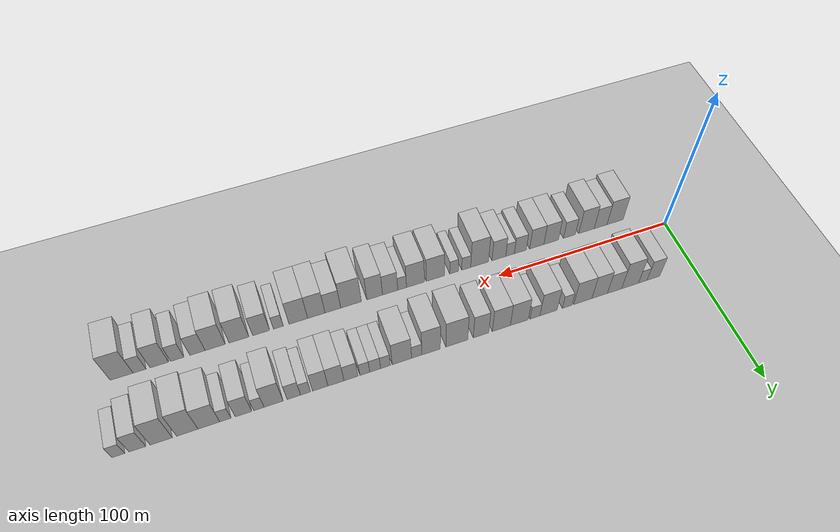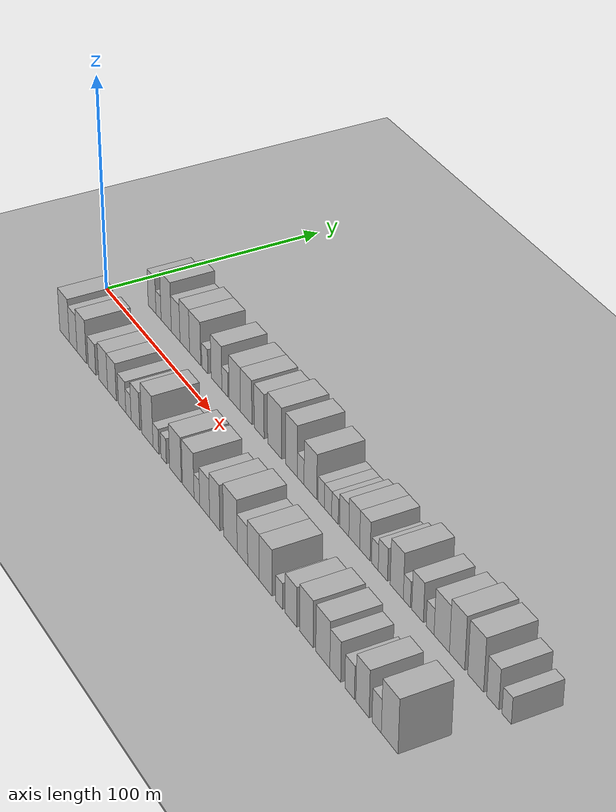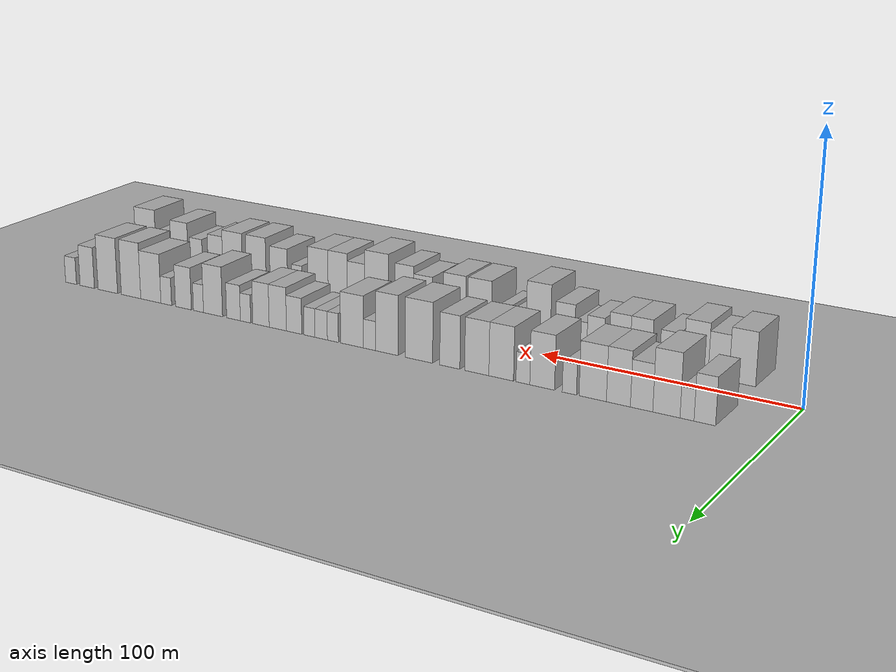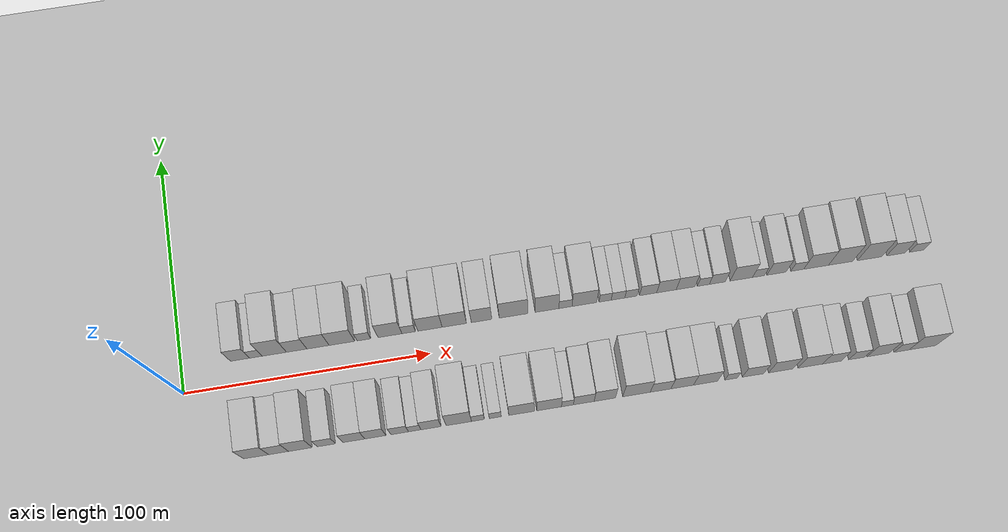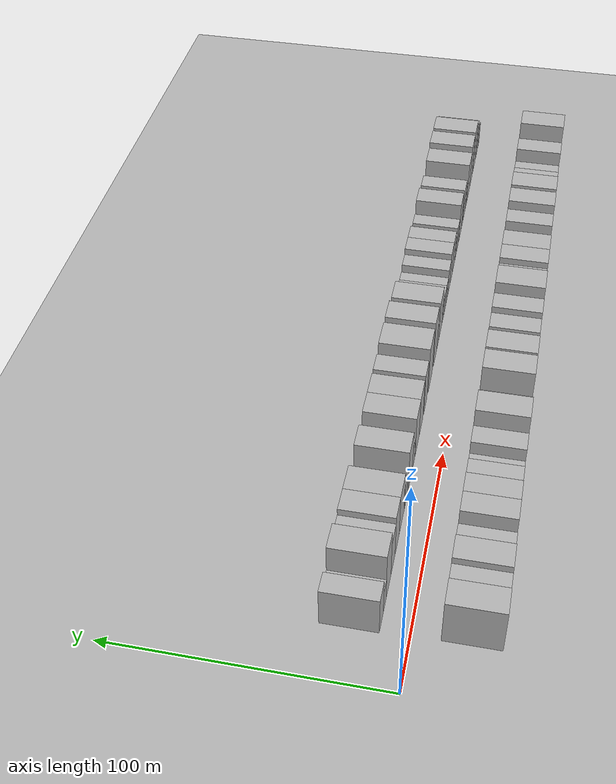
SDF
<?xml version="1.0" encoding="utf-8"?>

<sdf version="1.6">

   <world name="default">

      <gui fullscreen="0">

         <camera name="user_camera">

            <pose>-15 0 4.57585 0 0 0</pose>

            <view_controller>orbit</view_controller>

         </camera>

      </gui>

      <scene>

         <sky>

           <clouds>

             <speed>12</speed>

           </clouds>

         </sky>

         <ambient>0.4 0.4 0.4 1</ambient>

         <background>0.7 0.7 0.7 1</background>

         <shadows>1</shadows>

      </scene>

      <gravity>0 0 -9.8066</gravity>

      <magnetic_field>6e-06 2.3e-05 -4.2e-05</magnetic_field>

      <physics default="0" name="default_physics" type="ode">

         <ode>

            <solver>

               <type>quick</type>

               <iters>10</iters>

               <sor>1.0</sor>

               <use_dynamic_moi_rescaling>0</use_dynamic_moi_rescaling>

            </solver>

            <constraints>

               <cfm>0</cfm>

               <erp>0.2</erp>

               <contact_max_correcting_vel>100</contact_max_correcting_vel>

               <contact_surface_layer>0.001</contact_surface_layer>

            </constraints>

         </ode>

         <max_step_size>0.004</max_step_size>

         <real_time_factor>1</real_time_factor>

         <real_time_update_rate>250</real_time_update_rate>

      </physics>

      <light name="sun" type="directional">

         <cast_shadows>1</cast_shadows>

         <pose>0 0 10 0 0 0</pose>

         <diffuse>0.8 0.8 0.8 1</diffuse>

         <specular>0.2 0.2 0.2 1</specular>

         <attenuation>

            <range>1000</range>

            <constant>0.9</constant>

            <linear>0.01</linear>

            <quadratic>0.001</quadratic>

         </attenuation>

         <direction>-0.5 0.1 -0.9</direction>

      </light>

      <include>

         <name>ground_plane_1</name>

         <uri>model://HANNAS_ground_plane</uri>

         <pose>0 0 0  0 0 0</pose>

      </include>

      <include>

         <name>ground_plane_2</name>

         <uri>model://HANNAS_ground_plane</uri>

         <pose>100 0 0  0 0 0</pose>

      </include>

      <model name="building_1">

         <static>1</static>

         <pose frame="">23.8435 20.0000 0 0.000000 0.000000 1.570796</pose>

         <link name="link">

            <pose frame="">0 0 9.00 0 0 0</pose>

            <collision name="collision">

               <geometry>

                  <box>

                     <size>20.0000 7.6871 18.0000</size>

                  </box>

               </geometry>

               <max_contacts>10</max_contacts>

               <surface>

                  <contact>

                     <ode/>

                  </contact>

                  <bounce/>

                  <friction>

                     <torsional>

                        <ode/>

                     </torsional>

                     <ode/>

                  </friction>

               </surface>

            </collision>

            <visual name="visual">

               <cast_shadows>0</cast_shadows>

               <geometry>

                  <box>

                     <size>20.0000 7.6871 18.0000</size>

                  </box>

               </geometry>

               <material>

                  <script>

                     <uri>model://HANNAS_wall/materials/scripts</uri>

                     <uri>model://HANNAS_wall/materials/textures</uri>

                     <name>vrc/HANNAS_wall</name>

                  </script>

               </material>

            </visual>

            <self_collide>0</self_collide>

            <enable_wind>0</enable_wind>

            <kinematic>0</kinematic>

         </link>

      </model>

      <model name="building_2">

         <static>1</static>

         <pose frame="">30.2150 20.0000 0 0.000000 0.000000 1.570796</pose>

         <link name="link">

            <pose frame="">0 0 6.00 0 0 0</pose>

            <collision name="collision">

               <geometry>

                  <box>

                     <size>20.0000 5.0559 12.0000</size>

                  </box>

               </geometry>

               <max_contacts>10</max_contacts>

               <surface>

                  <contact>

                     <ode/>

                  </contact>

                  <bounce/>

                  <friction>

                     <torsional>

                        <ode/>

                     </torsional>

                     <ode/>

                  </friction>

               </surface>

            </collision>

            <visual name="visual">

               <cast_shadows>0</cast_shadows>

               <geometry>

                  <box>

                     <size>20.0000 5.0559 12.0000</size>

                  </box>

               </geometry>

               <material>

                  <script>

                     <uri>model://HANNAS_wall/materials/scripts</uri>

                     <uri>model://HANNAS_wall/materials/textures</uri>

                     <name>vrc/HANNAS_wall</name>

                  </script>

               </material>

            </visual>

            <self_collide>0</self_collide>

            <enable_wind>0</enable_wind>

            <kinematic>0</kinematic>

         </link>

      </model>

      <model name="building_3">

         <static>1</static>

         <pose frame="">37.7222 20.0000 0 0.000000 0.000000 1.570796</pose>

         <link name="link">

            <pose frame="">0 0 12.00 0 0 0</pose>

            <collision name="collision">

               <geometry>

                  <box>

                     <size>20.0000 9.9584 24.0000</size>

                  </box>

               </geometry>

               <max_contacts>10</max_contacts>

               <surface>

                  <contact>

                     <ode/>

                  </contact>

                  <bounce/>

                  <friction>

                     <torsional>

                        <ode/>

                     </torsional>

                     <ode/>

                  </friction>

               </surface>

            </collision>

            <visual name="visual">

               <cast_shadows>0</cast_shadows>

               <geometry>

                  <box>

                     <size>20.0000 9.9584 24.0000</size>

                  </box>

               </geometry>

               <material>

                  <script>

                     <uri>model://HANNAS_wall/materials/scripts</uri>

                     <uri>model://HANNAS_wall/materials/textures</uri>

                     <name>vrc/HANNAS_wall</name>

                  </script>

               </material>

            </visual>

            <self_collide>0</self_collide>

            <enable_wind>0</enable_wind>

            <kinematic>0</kinematic>

         </link>

      </model>

      <model name="building_4">

         <static>1</static>

         <pose frame="">46.8498 20.0000 0 0.000000 0.000000 1.570796</pose>

         <link name="link">

            <pose frame="">0 0 9.00 0 0 0</pose>

            <collision name="collision">

               <geometry>

                  <box>

                     <size>20.0000 8.2967 18.0000</size>

                  </box>

               </geometry>

               <max_contacts>10</max_contacts>

               <surface>

                  <contact>

                     <ode/>

                  </contact>

                  <bounce/>

                  <friction>

                     <torsional>

                        <ode/>

                     </torsional>

                     <ode/>

                  </friction>

               </surface>

            </collision>

            <visual name="visual">

               <cast_shadows>0</cast_shadows>

               <geometry>

                  <box>

                     <size>20.0000 8.2967 18.0000</size>

                  </box>

               </geometry>

               <material>

                  <script>

                     <uri>model://HANNAS_wall/materials/scripts</uri>

                     <uri>model://HANNAS_wall/materials/textures</uri>

                     <name>vrc/HANNAS_wall</name>

                  </script>

               </material>

            </visual>

            <self_collide>0</self_collide>

            <enable_wind>0</enable_wind>

            <kinematic>0</kinematic>

         </link>

      </model>

      <model name="building_5">

         <static>1</static>

         <pose frame="">55.5143 20.0000 0 0.000000 0.000000 1.570796</pose>

         <link name="link">

            <pose frame="">0 0 10.50 0 0 0</pose>

            <collision name="collision">

               <geometry>

                  <box>

                     <size>20.0000 9.0323 21.0000</size>

                  </box>

               </geometry>

               <max_contacts>10</max_contacts>

               <surface>

                  <contact>

                     <ode/>

                  </contact>

                  <bounce/>

                  <friction>

                     <torsional>

                        <ode/>

                     </torsional>

                     <ode/>

                  </friction>

               </surface>

            </collision>

            <visual name="visual">

               <cast_shadows>0</cast_shadows>

               <geometry>

                  <box>

                     <size>20.0000 9.0323 21.0000</size>

                  </box>

               </geometry>

               <material>

                  <script>

                     <uri>model://HANNAS_wall/materials/scripts</uri>

                     <uri>model://HANNAS_wall/materials/textures</uri>

                     <name>vrc/HANNAS_wall</name>

                  </script>

               </material>

            </visual>

            <self_collide>0</self_collide>

            <enable_wind>0</enable_wind>

            <kinematic>0</kinematic>

         </link>

      </model>

      <model name="building_6">

         <static>1</static>

         <pose frame="">65.2510 20.0000 0 0.000000 0.000000 1.570796</pose>

         <link name="link">

            <pose frame="">0 0 10.50 0 0 0</pose>

            <collision name="collision">

               <geometry>

                  <box>

                     <size>20.0000 10.4411 21.0000</size>

                  </box>

               </geometry>

               <max_contacts>10</max_contacts>

               <surface>

                  <contact>

                     <ode/>

                  </contact>

                  <bounce/>

                  <friction>

                     <torsional>

                        <ode/>

                     </torsional>

                     <ode/>

                  </friction>

               </surface>

            </collision>

            <visual name="visual">

               <cast_shadows>0</cast_shadows>

               <geometry>

                  <box>

                     <size>20.0000 10.4411 21.0000</size>

                  </box>

               </geometry>

               <material>

                  <script>

                     <uri>model://HANNAS_wall/materials/scripts</uri>

                     <uri>model://HANNAS_wall/materials/textures</uri>

                     <name>vrc/HANNAS_wall</name>

                  </script>

               </material>

            </visual>

            <self_collide>0</self_collide>

            <enable_wind>0</enable_wind>

            <kinematic>0</kinematic>

         </link>

      </model>

      <model name="building_7">

         <static>1</static>

         <pose frame="">74.2370 20.0000 0 0.000000 0.000000 1.570796</pose>

         <link name="link">

            <pose frame="">0 0 6.00 0 0 0</pose>

            <collision name="collision">

               <geometry>

                  <box>

                     <size>20.0000 5.5309 12.0000</size>

                  </box>

               </geometry>

               <max_contacts>10</max_contacts>

               <surface>

                  <contact>

                     <ode/>

                  </contact>

                  <bounce/>

                  <friction>

                     <torsional>

                        <ode/>

                     </torsional>

                     <ode/>

                  </friction>

               </surface>

            </collision>

            <visual name="visual">

               <cast_shadows>0</cast_shadows>

               <geometry>

                  <box>

                     <size>20.0000 5.5309 12.0000</size>

                  </box>

               </geometry>

               <material>

                  <script>

                     <uri>model://HANNAS_wall/materials/scripts</uri>

                     <uri>model://HANNAS_wall/materials/textures</uri>

                     <name>vrc/HANNAS_wall</name>

                  </script>

               </material>

            </visual>

            <self_collide>0</self_collide>

            <enable_wind>0</enable_wind>

            <kinematic>0</kinematic>

         </link>

      </model>

      <model name="building_8">

         <static>1</static>

         <pose frame="">84.8800 20.0000 0 0.000000 0.000000 1.570796</pose>

         <link name="link">

            <pose frame="">0 0 10.50 0 0 0</pose>

            <collision name="collision">

               <geometry>

                  <box>

                     <size>20.0000 9.7551 21.0000</size>

                  </box>

               </geometry>

               <max_contacts>10</max_contacts>

               <surface>

                  <contact>

                     <ode/>

                  </contact>

                  <bounce/>

                  <friction>

                     <torsional>

                        <ode/>

                     </torsional>

                     <ode/>

                  </friction>

               </surface>

            </collision>

            <visual name="visual">

               <cast_shadows>0</cast_shadows>

               <geometry>

                  <box>

                     <size>20.0000 9.7551 21.0000</size>

                  </box>

               </geometry>

               <material>

                  <script>

                     <uri>model://HANNAS_wall/materials/scripts</uri>

                     <uri>model://HANNAS_wall/materials/textures</uri>

                     <name>vrc/HANNAS_wall</name>

                  </script>

               </material>

            </visual>

            <self_collide>0</self_collide>

            <enable_wind>0</enable_wind>

            <kinematic>0</kinematic>

         </link>

      </model>

      <model name="building_9">

         <static>1</static>

         <pose frame="">92.5117 20.0000 0 0.000000 0.000000 1.570796</pose>

         <link name="link">

            <pose frame="">0 0 6.00 0 0 0</pose>

            <collision name="collision">

               <geometry>

                  <box>

                     <size>20.0000 5.5084 12.0000</size>

                  </box>

               </geometry>

               <max_contacts>10</max_contacts>

               <surface>

                  <contact>

                     <ode/>

                  </contact>

                  <bounce/>

                  <friction>

                     <torsional>

                        <ode/>

                     </torsional>

                     <ode/>

                  </friction>

               </surface>

            </collision>

            <visual name="visual">

               <cast_shadows>0</cast_shadows>

               <geometry>

                  <box>

                     <size>20.0000 5.5084 12.0000</size>

                  </box>

               </geometry>

               <material>

                  <script>

                     <uri>model://HANNAS_wall/materials/scripts</uri>

                     <uri>model://HANNAS_wall/materials/textures</uri>

                     <name>vrc/HANNAS_wall</name>

                  </script>

               </material>

            </visual>

            <self_collide>0</self_collide>

            <enable_wind>0</enable_wind>

            <kinematic>0</kinematic>

         </link>

      </model>

      <model name="building_10">

         <static>1</static>

         <pose frame="">101.2545 20.0000 0 0.000000 0.000000 1.570796</pose>

         <link name="link">

            <pose frame="">0 0 10.50 0 0 0</pose>

            <collision name="collision">

               <geometry>

                  <box>

                     <size>20.0000 9.9771 21.0000</size>

                  </box>

               </geometry>

               <max_contacts>10</max_contacts>

               <surface>

                  <contact>

                     <ode/>

                  </contact>

                  <bounce/>

                  <friction>

                     <torsional>

                        <ode/>

                     </torsional>

                     <ode/>

                  </friction>

               </surface>

            </collision>

            <visual name="visual">

               <cast_shadows>0</cast_shadows>

               <geometry>

                  <box>

                     <size>20.0000 9.9771 21.0000</size>

                  </box>

               </geometry>

               <material>

                  <script>

                     <uri>model://HANNAS_wall/materials/scripts</uri>

                     <uri>model://HANNAS_wall/materials/textures</uri>

                     <name>vrc/HANNAS_wall</name>

                  </script>

               </material>

            </visual>

            <self_collide>0</self_collide>

            <enable_wind>0</enable_wind>

            <kinematic>0</kinematic>

         </link>

      </model>

      <model name="building_11">

         <static>1</static>

         <pose frame="">111.2242 20.0000 0 0.000000 0.000000 1.570796</pose>

         <link name="link">

            <pose frame="">0 0 10.50 0 0 0</pose>

            <collision name="collision">

               <geometry>

                  <box>

                     <size>20.0000 9.9622 21.0000</size>

                  </box>

               </geometry>

               <max_contacts>10</max_contacts>

               <surface>

                  <contact>

                     <ode/>

                  </contact>

                  <bounce/>

                  <friction>

                     <torsional>

                        <ode/>

                     </torsional>

                     <ode/>

                  </friction>

               </surface>

            </collision>

            <visual name="visual">

               <cast_shadows>0</cast_shadows>

               <geometry>

                  <box>

                     <size>20.0000 9.9622 21.0000</size>

                  </box>

               </geometry>

               <material>

                  <script>

                     <uri>model://HANNAS_wall/materials/scripts</uri>

                     <uri>model://HANNAS_wall/materials/textures</uri>

                     <name>vrc/HANNAS_wall</name>

                  </script>

               </material>

            </visual>

            <self_collide>0</self_collide>

            <enable_wind>0</enable_wind>

            <kinematic>0</kinematic>

         </link>

      </model>

      <model name="building_12">

         <static>1</static>

         <pose frame="">122.4271 20.0000 0 0.000000 0.000000 1.570796</pose>

         <link name="link">

            <pose frame="">0 0 10.50 0 0 0</pose>

            <collision name="collision">

               <geometry>

                  <box>

                     <size>20.0000 8.4437 21.0000</size>

                  </box>

               </geometry>

               <max_contacts>10</max_contacts>

               <surface>

                  <contact>

                     <ode/>

                  </contact>

                  <bounce/>

                  <friction>

                     <torsional>

                        <ode/>

                     </torsional>

                     <ode/>

                  </friction>

               </surface>

            </collision>

            <visual name="visual">

               <cast_shadows>0</cast_shadows>

               <geometry>

                  <box>

                     <size>20.0000 8.4437 21.0000</size>

                  </box>

               </geometry>

               <material>

                  <script>

                     <uri>model://HANNAS_wall/materials/scripts</uri>

                     <uri>model://HANNAS_wall/materials/textures</uri>

                     <name>vrc/HANNAS_wall</name>

                  </script>

               </material>

            </visual>

            <self_collide>0</self_collide>

            <enable_wind>0</enable_wind>

            <kinematic>0</kinematic>

         </link>

      </model>

      <model name="building_13">

         <static>1</static>

         <pose frame="">135.5499 20.0000 0 0.000000 0.000000 1.570796</pose>

         <link name="link">

            <pose frame="">0 0 12.00 0 0 0</pose>

            <collision name="collision">

               <geometry>

                  <box>

                     <size>20.0000 11.8019 24.0000</size>

                  </box>

               </geometry>

               <max_contacts>10</max_contacts>

               <surface>

                  <contact>

                     <ode/>

                  </contact>

                  <bounce/>

                  <friction>

                     <torsional>

                        <ode/>

                     </torsional>

                     <ode/>

                  </friction>

               </surface>

            </collision>

            <visual name="visual">

               <cast_shadows>0</cast_shadows>

               <geometry>

                  <box>

                     <size>20.0000 11.8019 24.0000</size>

                  </box>

               </geometry>

               <material>

                  <script>

                     <uri>model://HANNAS_wall/materials/scripts</uri>

                     <uri>model://HANNAS_wall/materials/textures</uri>

                     <name>vrc/HANNAS_wall</name>

                  </script>

               </material>

            </visual>

            <self_collide>0</self_collide>

            <enable_wind>0</enable_wind>

            <kinematic>0</kinematic>

         </link>

      </model>

      <model name="building_14">

         <static>1</static>

         <pose frame="">149.3508 20.0000 0 0.000000 0.000000 1.570796</pose>

         <link name="link">

            <pose frame="">0 0 12.00 0 0 0</pose>

            <collision name="collision">

               <geometry>

                  <box>

                     <size>20.0000 9.7998 24.0000</size>

                  </box>

               </geometry>

               <max_contacts>10</max_contacts>

               <surface>

                  <contact>

                     <ode/>

                  </contact>

                  <bounce/>

                  <friction>

                     <torsional>

                        <ode/>

                     </torsional>

                     <ode/>

                  </friction>

               </surface>

            </collision>

            <visual name="visual">

               <cast_shadows>0</cast_shadows>

               <geometry>

                  <box>

                     <size>20.0000 9.7998 24.0000</size>

                  </box>

               </geometry>

               <material>

                  <script>

                     <uri>model://HANNAS_wall/materials/scripts</uri>

                     <uri>model://HANNAS_wall/materials/textures</uri>

                     <name>vrc/HANNAS_wall</name>

                  </script>

               </material>

            </visual>

            <self_collide>0</self_collide>

            <enable_wind>0</enable_wind>

            <kinematic>0</kinematic>

         </link>

      </model>

      <model name="building_15">

         <static>1</static>

         <pose frame="">156.9666 20.0000 0 0.000000 0.000000 1.570796</pose>

         <link name="link">

            <pose frame="">0 0 6.00 0 0 0</pose>

            <collision name="collision">

               <geometry>

                  <box>

                     <size>20.0000 5.4317 12.0000</size>

                  </box>

               </geometry>

               <max_contacts>10</max_contacts>

               <surface>

                  <contact>

                     <ode/>

                  </contact>

                  <bounce/>

                  <friction>

                     <torsional>

                        <ode/>

                     </torsional>

                     <ode/>

                  </friction>

               </surface>

            </collision>

            <visual name="visual">

               <cast_shadows>0</cast_shadows>

               <geometry>

                  <box>

                     <size>20.0000 5.4317 12.0000</size>

                  </box>

               </geometry>

               <material>

                  <script>

                     <uri>model://HANNAS_wall/materials/scripts</uri>

                     <uri>model://HANNAS_wall/materials/textures</uri>

                     <name>vrc/HANNAS_wall</name>

                  </script>

               </material>

            </visual>

            <self_collide>0</self_collide>

            <enable_wind>0</enable_wind>

            <kinematic>0</kinematic>

         </link>

      </model>

      <model name="building_16">

         <static>1</static>

         <pose frame="">164.7859 20.0000 0 0.000000 0.000000 1.570796</pose>

         <link name="link">

            <pose frame="">0 0 10.50 0 0 0</pose>

            <collision name="collision">

               <geometry>

                  <box>

                     <size>20.0000 10.2070 21.0000</size>

                  </box>

               </geometry>

               <max_contacts>10</max_contacts>

               <surface>

                  <contact>

                     <ode/>

                  </contact>

                  <bounce/>

                  <friction>

                     <torsional>

                        <ode/>

                     </torsional>

                     <ode/>

                  </friction>

               </surface>

            </collision>

            <visual name="visual">

               <cast_shadows>0</cast_shadows>

               <geometry>

                  <box>

                     <size>20.0000 10.2070 21.0000</size>

                  </box>

               </geometry>

               <material>

                  <script>

                     <uri>model://HANNAS_wall/materials/scripts</uri>

                     <uri>model://HANNAS_wall/materials/textures</uri>

                     <name>vrc/HANNAS_wall</name>

                  </script>

               </material>

            </visual>

            <self_collide>0</self_collide>

            <enable_wind>0</enable_wind>

            <kinematic>0</kinematic>

         </link>

      </model>

      <model name="building_17">

         <static>1</static>

         <pose frame="">173.3860 20.0000 0 0.000000 0.000000 1.570796</pose>

         <link name="link">

            <pose frame="">0 0 6.00 0 0 0</pose>

            <collision name="collision">

               <geometry>

                  <box>

                     <size>20.0000 4.9933 12.0000</size>

                  </box>

               </geometry>

               <max_contacts>10</max_contacts>

               <surface>

                  <contact>

                     <ode/>

                  </contact>

                  <bounce/>

                  <friction>

                     <torsional>

                        <ode/>

                     </torsional>

                     <ode/>

                  </friction>

               </surface>

            </collision>

            <visual name="visual">

               <cast_shadows>0</cast_shadows>

               <geometry>

                  <box>

                     <size>20.0000 4.9933 12.0000</size>

                  </box>

               </geometry>

               <material>

                  <script>

                     <uri>model://HANNAS_wall/materials/scripts</uri>

                     <uri>model://HANNAS_wall/materials/textures</uri>

                     <name>vrc/HANNAS_wall</name>

                  </script>

               </material>

            </visual>

            <self_collide>0</self_collide>

            <enable_wind>0</enable_wind>

            <kinematic>0</kinematic>

         </link>

      </model>

      <model name="building_18">

         <static>1</static>

         <pose frame="">178.7066 20.0000 0 0.000000 0.000000 1.570796</pose>

         <link name="link">

            <pose frame="">0 0 6.00 0 0 0</pose>

            <collision name="collision">

               <geometry>

                  <box>

                     <size>20.0000 5.6479 12.0000</size>

                  </box>

               </geometry>

               <max_contacts>10</max_contacts>

               <surface>

                  <contact>

                     <ode/>

                  </contact>

                  <bounce/>

                  <friction>

                     <torsional>

                        <ode/>

                     </torsional>

                     <ode/>

                  </friction>

               </surface>

            </collision>

            <visual name="visual">

               <cast_shadows>0</cast_shadows>

               <geometry>

                  <box>

                     <size>20.0000 5.6479 12.0000</size>

                  </box>

               </geometry>

               <material>

                  <script>

                     <uri>model://HANNAS_wall/materials/scripts</uri>

                     <uri>model://HANNAS_wall/materials/textures</uri>

                     <name>vrc/HANNAS_wall</name>

                  </script>

               </material>

            </visual>

            <self_collide>0</self_collide>

            <enable_wind>0</enable_wind>

            <kinematic>0</kinematic>

         </link>

      </model>

      <model name="building_19">

         <static>1</static>

         <pose frame="">184.0761 20.0000 0 0.000000 0.000000 1.570796</pose>

         <link name="link">

            <pose frame="">0 0 6.00 0 0 0</pose>

            <collision name="collision">

               <geometry>

                  <box>

                     <size>20.0000 5.0911 12.0000</size>

                  </box>

               </geometry>

               <max_contacts>10</max_contacts>

               <surface>

                  <contact>

                     <ode/>

                  </contact>

                  <bounce/>

                  <friction>

                     <torsional>

                        <ode/>

                     </torsional>

                     <ode/>

                  </friction>

               </surface>

            </collision>

            <visual name="visual">

               <cast_shadows>0</cast_shadows>

               <geometry>

                  <box>

                     <size>20.0000 5.0911 12.0000</size>

                  </box>

               </geometry>

               <material>

                  <script>

                     <uri>model://HANNAS_wall/materials/scripts</uri>

                     <uri>model://HANNAS_wall/materials/textures</uri>

                     <name>vrc/HANNAS_wall</name>

                  </script>

               </material>

            </visual>

            <self_collide>0</self_collide>

            <enable_wind>0</enable_wind>

            <kinematic>0</kinematic>

         </link>

      </model>

      <model name="building_20">

         <static>1</static>

         <pose frame="">191.1918 20.0000 0 0.000000 0.000000 1.570796</pose>

         <link name="link">

            <pose frame="">0 0 7.50 0 0 0</pose>

            <collision name="collision">

               <geometry>

                  <box>

                     <size>20.0000 7.1403 15.0000</size>

                  </box>

               </geometry>

               <max_contacts>10</max_contacts>

               <surface>

                  <contact>

                     <ode/>

                  </contact>

                  <bounce/>

                  <friction>

                     <torsional>

                        <ode/>

                     </torsional>

                     <ode/>

                  </friction>

               </surface>

            </collision>

            <visual name="visual">

               <cast_shadows>0</cast_shadows>

               <geometry>

                  <box>

                     <size>20.0000 7.1403 15.0000</size>

                  </box>

               </geometry>

               <material>

                  <script>

                     <uri>model://HANNAS_wall/materials/scripts</uri>

                     <uri>model://HANNAS_wall/materials/textures</uri>

                     <name>vrc/HANNAS_wall</name>

                  </script>

               </material>

            </visual>

            <self_collide>0</self_collide>

            <enable_wind>0</enable_wind>

            <kinematic>0</kinematic>

         </link>

      </model>

      <model name="building_21">

         <static>1</static>

         <pose frame="">198.8291 20.0000 0 0.000000 0.000000 1.570796</pose>

         <link name="link">

            <pose frame="">0 0 9.00 0 0 0</pose>

            <collision name="collision">

               <geometry>

                  <box>

                     <size>20.0000 8.1343 18.0000</size>

                  </box>

               </geometry>

               <max_contacts>10</max_contacts>

               <surface>

                  <contact>

                     <ode/>

                  </contact>

                  <bounce/>

                  <friction>

                     <torsional>

                        <ode/>

                     </torsional>

                     <ode/>

                  </friction>

               </surface>

            </collision>

            <visual name="visual">

               <cast_shadows>0</cast_shadows>

               <geometry>

                  <box>

                     <size>20.0000 8.1343 18.0000</size>

                  </box>

               </geometry>

               <material>

                  <script>

                     <uri>model://HANNAS_wall/materials/scripts</uri>

                     <uri>model://HANNAS_wall/materials/textures</uri>

                     <name>vrc/HANNAS_wall</name>

                  </script>

               </material>

            </visual>

            <self_collide>0</self_collide>

            <enable_wind>0</enable_wind>

            <kinematic>0</kinematic>

         </link>

      </model>

      <model name="building_22">

         <static>1</static>

         <pose frame="">206.7928 20.0000 0 0.000000 0.000000 1.570796</pose>

         <link name="link">

            <pose frame="">0 0 9.00 0 0 0</pose>

            <collision name="collision">

               <geometry>

                  <box>

                     <size>20.0000 7.7930 18.0000</size>

                  </box>

               </geometry>

               <max_contacts>10</max_contacts>

               <surface>

                  <contact>

                     <ode/>

                  </contact>

                  <bounce/>

                  <friction>

                     <torsional>

                        <ode/>

                     </torsional>

                     <ode/>

                  </friction>

               </surface>

            </collision>

            <visual name="visual">

               <cast_shadows>0</cast_shadows>

               <geometry>

                  <box>

                     <size>20.0000 7.7930 18.0000</size>

                  </box>

               </geometry>

               <material>

                  <script>

                     <uri>model://HANNAS_wall/materials/scripts</uri>

                     <uri>model://HANNAS_wall/materials/textures</uri>

                     <name>vrc/HANNAS_wall</name>

                  </script>

               </material>

            </visual>

            <self_collide>0</self_collide>

            <enable_wind>0</enable_wind>

            <kinematic>0</kinematic>

         </link>

      </model>

      <model name="building_23">

         <static>1</static>

         <pose frame="">214.1908 20.0000 0 0.000000 0.000000 1.570796</pose>

         <link name="link">

            <pose frame="">0 0 6.00 0 0 0</pose>

            <collision name="collision">

               <geometry>

                  <box>

                     <size>20.0000 5.0030 12.0000</size>

                  </box>

               </geometry>

               <max_contacts>10</max_contacts>

               <surface>

                  <contact>

                     <ode/>

                  </contact>

                  <bounce/>

                  <friction>

                     <torsional>

                        <ode/>

                     </torsional>

                     <ode/>

                  </friction>

               </surface>

            </collision>

            <visual name="visual">

               <cast_shadows>0</cast_shadows>

               <geometry>

                  <box>

                     <size>20.0000 5.0030 12.0000</size>

                  </box>

               </geometry>

               <material>

                  <script>

                     <uri>model://HANNAS_wall/materials/scripts</uri>

                     <uri>model://HANNAS_wall/materials/textures</uri>

                     <name>vrc/HANNAS_wall</name>

                  </script>

               </material>

            </visual>

            <self_collide>0</self_collide>

            <enable_wind>0</enable_wind>

            <kinematic>0</kinematic>

         </link>

      </model>

      <model name="building_24">

         <static>1</static>

         <pose frame="">220.0308 20.0000 0 0.000000 0.000000 1.570796</pose>

         <link name="link">

            <pose frame="">0 0 7.50 0 0 0</pose>

            <collision name="collision">

               <geometry>

                  <box>

                     <size>20.0000 6.6769 15.0000</size>

                  </box>

               </geometry>

               <max_contacts>10</max_contacts>

               <surface>

                  <contact>

                     <ode/>

                  </contact>

                  <bounce/>

                  <friction>

                     <torsional>

                        <ode/>

                     </torsional>

                     <ode/>

                  </friction>

               </surface>

            </collision>

            <visual name="visual">

               <cast_shadows>0</cast_shadows>

               <geometry>

                  <box>

                     <size>20.0000 6.6769 15.0000</size>

                  </box>

               </geometry>

               <material>

                  <script>

                     <uri>model://HANNAS_wall/materials/scripts</uri>

                     <uri>model://HANNAS_wall/materials/textures</uri>

                     <name>vrc/HANNAS_wall</name>

                  </script>

               </material>

            </visual>

            <self_collide>0</self_collide>

            <enable_wind>0</enable_wind>

            <kinematic>0</kinematic>

         </link>

      </model>

      <model name="building_25">

         <static>1</static>

         <pose frame="">230.0644 20.0000 0 0.000000 0.000000 1.570796</pose>

         <link name="link">

            <pose frame="">0 0 10.50 0 0 0</pose>

            <collision name="collision">

               <geometry>

                  <box>

                     <size>20.0000 9.3903 21.0000</size>

                  </box>

               </geometry>

               <max_contacts>10</max_contacts>

               <surface>

                  <contact>

                     <ode/>

                  </contact>

                  <bounce/>

                  <friction>

                     <torsional>

                        <ode/>

                     </torsional>

                     <ode/>

                  </friction>

               </surface>

            </collision>

            <visual name="visual">

               <cast_shadows>0</cast_shadows>

               <geometry>

                  <box>

                     <size>20.0000 9.3903 21.0000</size>

                  </box>

               </geometry>

               <material>

                  <script>

                     <uri>model://HANNAS_wall/materials/scripts</uri>

                     <uri>model://HANNAS_wall/materials/textures</uri>

                     <name>vrc/HANNAS_wall</name>

                  </script>

               </material>

            </visual>

            <self_collide>0</self_collide>

            <enable_wind>0</enable_wind>

            <kinematic>0</kinematic>

         </link>

      </model>

      <model name="building_26">

         <static>1</static>

         <pose frame="">237.2728 20.0000 0 0.000000 0.000000 1.570796</pose>

         <link name="link">

            <pose frame="">0 0 6.00 0 0 0</pose>

            <collision name="collision">

               <geometry>

                  <box>

                     <size>20.0000 5.0264 12.0000</size>

                  </box>

               </geometry>

               <max_contacts>10</max_contacts>

               <surface>

                  <contact>

                     <ode/>

                  </contact>

                  <bounce/>

                  <friction>

                     <torsional>

                        <ode/>

                     </torsional>

                     <ode/>

                  </friction>

               </surface>

            </collision>

            <visual name="visual">

               <cast_shadows>0</cast_shadows>

               <geometry>

                  <box>

                     <size>20.0000 5.0264 12.0000</size>

                  </box>

               </geometry>

               <material>

                  <script>

                     <uri>model://HANNAS_wall/materials/scripts</uri>

                     <uri>model://HANNAS_wall/materials/textures</uri>

                     <name>vrc/HANNAS_wall</name>

                  </script>

               </material>

            </visual>

            <self_collide>0</self_collide>

            <enable_wind>0</enable_wind>

            <kinematic>0</kinematic>

         </link>

      </model>

      <model name="building_27">

         <static>1</static>

         <pose frame="">244.8036 20.0000 0 0.000000 0.000000 1.570796</pose>

         <link name="link">

            <pose frame="">0 0 9.00 0 0 0</pose>

            <collision name="collision">

               <geometry>

                  <box>

                     <size>20.0000 8.0354 18.0000</size>

                  </box>

               </geometry>

               <max_contacts>10</max_contacts>

               <surface>

                  <contact>

                     <ode/>

                  </contact>

                  <bounce/>

                  <friction>

                     <torsional>

                        <ode/>

                     </torsional>

                     <ode/>

                  </friction>

               </surface>

            </collision>

            <visual name="visual">

               <cast_shadows>0</cast_shadows>

               <geometry>

                  <box>

                     <size>20.0000 8.0354 18.0000</size>

                  </box>

               </geometry>

               <material>

                  <script>

                     <uri>model://HANNAS_wall/materials/scripts</uri>

                     <uri>model://HANNAS_wall/materials/textures</uri>

                     <name>vrc/HANNAS_wall</name>

                  </script>

               </material>

            </visual>

            <self_collide>0</self_collide>

            <enable_wind>0</enable_wind>

            <kinematic>0</kinematic>

         </link>

      </model>

      <model name="building_28">

         <static>1</static>

         <pose frame="">253.5256 20.0000 0 0.000000 0.000000 1.570796</pose>

         <link name="link">

            <pose frame="">0 0 6.00 0 0 0</pose>

            <collision name="collision">

               <geometry>

                  <box>

                     <size>20.0000 5.4085 12.0000</size>

                  </box>

               </geometry>

               <max_contacts>10</max_contacts>

               <surface>

                  <contact>

                     <ode/>

                  </contact>

                  <bounce/>

                  <friction>

                     <torsional>

                        <ode/>

                     </torsional>

                     <ode/>

                  </friction>

               </surface>

            </collision>

            <visual name="visual">

               <cast_shadows>0</cast_shadows>

               <geometry>

                  <box>

                     <size>20.0000 5.4085 12.0000</size>

                  </box>

               </geometry>

               <material>

                  <script>

                     <uri>model://HANNAS_wall/materials/scripts</uri>

                     <uri>model://HANNAS_wall/materials/textures</uri>

                     <name>vrc/HANNAS_wall</name>

                  </script>

               </material>

            </visual>

            <self_collide>0</self_collide>

            <enable_wind>0</enable_wind>

            <kinematic>0</kinematic>

         </link>

      </model>

      <model name="building_29">

         <static>1</static>

         <pose frame="">261.4427 20.0000 0 0.000000 0.000000 1.570796</pose>

         <link name="link">

            <pose frame="">0 0 10.50 0 0 0</pose>

            <collision name="collision">

               <geometry>

                  <box>

                     <size>20.0000 10.4257 21.0000</size>

                  </box>

               </geometry>

               <max_contacts>10</max_contacts>

               <surface>

                  <contact>

                     <ode/>

                  </contact>

                  <bounce/>

                  <friction>

                     <torsional>

                        <ode/>

                     </torsional>

                     <ode/>

                  </friction>

               </surface>

            </collision>

            <visual name="visual">

               <cast_shadows>0</cast_shadows>

               <geometry>

                  <box>

                     <size>20.0000 10.4257 21.0000</size>

                  </box>

               </geometry>

               <material>

                  <script>

                     <uri>model://HANNAS_wall/materials/scripts</uri>

                     <uri>model://HANNAS_wall/materials/textures</uri>

                     <name>vrc/HANNAS_wall</name>

                  </script>

               </material>

            </visual>

            <self_collide>0</self_collide>

            <enable_wind>0</enable_wind>

            <kinematic>0</kinematic>

         </link>

      </model>

      <model name="building_30">

         <static>1</static>

         <pose frame="">271.7292 20.0000 0 0.000000 0.000000 1.570796</pose>

         <link name="link">

            <pose frame="">0 0 12.00 0 0 0</pose>

            <collision name="collision">

               <geometry>

                  <box>

                     <size>20.0000 10.1475 24.0000</size>

                  </box>

               </geometry>

               <max_contacts>10</max_contacts>

               <surface>

                  <contact>

                     <ode/>

                  </contact>

                  <bounce/>

                  <friction>

                     <torsional>

                        <ode/>

                     </torsional>

                     <ode/>

                  </friction>

               </surface>

            </collision>

            <visual name="visual">

               <cast_shadows>0</cast_shadows>

               <geometry>

                  <box>

                     <size>20.0000 10.1475 24.0000</size>

                  </box>

               </geometry>

               <material>

                  <script>

                     <uri>model://HANNAS_wall/materials/scripts</uri>

                     <uri>model://HANNAS_wall/materials/textures</uri>

                     <name>vrc/HANNAS_wall</name>

                  </script>

               </material>

            </visual>

            <self_collide>0</self_collide>

            <enable_wind>0</enable_wind>

            <kinematic>0</kinematic>

         </link>

      </model>

      <model name="building_31">

         <static>1</static>

         <pose frame="">283.9838 20.0000 0 0.000000 0.000000 1.570796</pose>

         <link name="link">

            <pose frame="">0 0 12.00 0 0 0</pose>

            <collision name="collision">

               <geometry>

                  <box>

                     <size>20.0000 10.3616 24.0000</size>

                  </box>

               </geometry>

               <max_contacts>10</max_contacts>

               <surface>

                  <contact>

                     <ode/>

                  </contact>

                  <bounce/>

                  <friction>

                     <torsional>

                        <ode/>

                     </torsional>

                     <ode/>

                  </friction>

               </surface>

            </collision>

            <visual name="visual">

               <cast_shadows>0</cast_shadows>

               <geometry>

                  <box>

                     <size>20.0000 10.3616 24.0000</size>

                  </box>

               </geometry>

               <material>

                  <script>

                     <uri>model://HANNAS_wall/materials/scripts</uri>

                     <uri>model://HANNAS_wall/materials/textures</uri>

                     <name>vrc/HANNAS_wall</name>

                  </script>

               </material>

            </visual>

            <self_collide>0</self_collide>

            <enable_wind>0</enable_wind>

            <kinematic>0</kinematic>

         </link>

      </model>

      <model name="building_32">

         <static>1</static>

         <pose frame="">295.0249 20.0000 0 0.000000 0.000000 1.570796</pose>

         <link name="link">

            <pose frame="">0 0 9.00 0 0 0</pose>

            <collision name="collision">

               <geometry>

                  <box>

                     <size>20.0000 7.7207 18.0000</size>

                  </box>

               </geometry>

               <max_contacts>10</max_contacts>

               <surface>

                  <contact>

                     <ode/>

                  </contact>

                  <bounce/>

                  <friction>

                     <torsional>

                        <ode/>

                     </torsional>

                     <ode/>

                  </friction>

               </surface>

            </collision>

            <visual name="visual">

               <cast_shadows>0</cast_shadows>

               <geometry>

                  <box>

                     <size>20.0000 7.7207 18.0000</size>

                  </box>

               </geometry>

               <material>

                  <script>

                     <uri>model://HANNAS_wall/materials/scripts</uri>

                     <uri>model://HANNAS_wall/materials/textures</uri>

                     <name>vrc/HANNAS_wall</name>

                  </script>

               </material>

            </visual>

            <self_collide>0</self_collide>

            <enable_wind>0</enable_wind>

            <kinematic>0</kinematic>

         </link>

      </model>

      <model name="building_33">

         <static>1</static>

         <pose frame="">303.8364 20.0000 0 0.000000 0.000000 1.570796</pose>

         <link name="link">

            <pose frame="">0 0 6.00 0 0 0</pose>

            <collision name="collision">

               <geometry>

                  <box>

                     <size>20.0000 5.9021 12.0000</size>

                  </box>

               </geometry>

               <max_contacts>10</max_contacts>

               <surface>

                  <contact>

                     <ode/>

                  </contact>

                  <bounce/>

                  <friction>

                     <torsional>

                        <ode/>

                     </torsional>

                     <ode/>

                  </friction>

               </surface>

            </collision>

            <visual name="visual">

               <cast_shadows>0</cast_shadows>

               <geometry>

                  <box>

                     <size>20.0000 5.9021 12.0000</size>

                  </box>

               </geometry>

               <material>

                  <script>

                     <uri>model://HANNAS_wall/materials/scripts</uri>

                     <uri>model://HANNAS_wall/materials/textures</uri>

                     <name>vrc/HANNAS_wall</name>

                  </script>

               </material>

            </visual>

            <self_collide>0</self_collide>

            <enable_wind>0</enable_wind>

            <kinematic>0</kinematic>

         </link>

      </model>

      <model name="building_34">

         <static>1</static>

         <pose frame="">25.9748 -20.0000 0 0.000000 0.000000 1.570796</pose>

         <link name="link">

            <pose frame="">0 0 10.50 0 0 0</pose>

            <collision name="collision">

               <geometry>

                  <box>

                     <size>20.0000 9.9496 21.0000</size>

                  </box>

               </geometry>

               <max_contacts>10</max_contacts>

               <surface>

                  <contact>

                     <ode/>

                  </contact>

                  <bounce/>

                  <friction>

                     <torsional>

                        <ode/>

                     </torsional>

                     <ode/>

                  </friction>

               </surface>

            </collision>

            <visual name="visual">

               <cast_shadows>0</cast_shadows>

               <geometry>

                  <box>

                     <size>20.0000 9.9496 21.0000</size>

                  </box>

               </geometry>

               <material>

                  <script>

                     <uri>model://HANNAS_wall/materials/scripts</uri>

                     <uri>model://HANNAS_wall/materials/textures</uri>

                     <name>vrc/HANNAS_wall</name>

                  </script>

               </material>

            </visual>

            <self_collide>0</self_collide>

            <enable_wind>0</enable_wind>

            <kinematic>0</kinematic>

         </link>

      </model>

      <model name="building_35">

         <static>1</static>

         <pose frame="">34.9045 -20.0000 0 0.000000 0.000000 1.570796</pose>

         <link name="link">

            <pose frame="">0 0 9.00 0 0 0</pose>

            <collision name="collision">

               <geometry>

                  <box>

                     <size>20.0000 7.9098 18.0000</size>

                  </box>

               </geometry>

               <max_contacts>10</max_contacts>

               <surface>

                  <contact>

                     <ode/>

                  </contact>

                  <bounce/>

                  <friction>

                     <torsional>

                        <ode/>

                     </torsional>

                     <ode/>

                  </friction>

               </surface>

            </collision>

            <visual name="visual">

               <cast_shadows>0</cast_shadows>

               <geometry>

                  <box>

                     <size>20.0000 7.9098 18.0000</size>

                  </box>

               </geometry>

               <material>

                  <script>

                     <uri>model://HANNAS_wall/materials/scripts</uri>

                     <uri>model://HANNAS_wall/materials/textures</uri>

                     <name>vrc/HANNAS_wall</name>

                  </script>

               </material>

            </visual>

            <self_collide>0</self_collide>

            <enable_wind>0</enable_wind>

            <kinematic>0</kinematic>

         </link>

      </model>

      <model name="building_36">

         <static>1</static>

         <pose frame="">43.5844 -20.0000 0 0.000000 0.000000 1.570796</pose>

         <link name="link">

            <pose frame="">0 0 10.50 0 0 0</pose>

            <collision name="collision">

               <geometry>

                  <box>

                     <size>20.0000 9.4499 21.0000</size>

                  </box>

               </geometry>

               <max_contacts>10</max_contacts>

               <surface>

                  <contact>

                     <ode/>

                  </contact>

                  <bounce/>

                  <friction>

                     <torsional>

                        <ode/>

                     </torsional>

                     <ode/>

                  </friction>

               </surface>

            </collision>

            <visual name="visual">

               <cast_shadows>0</cast_shadows>

               <geometry>

                  <box>

                     <size>20.0000 9.4499 21.0000</size>

                  </box>

               </geometry>

               <material>

                  <script>

                     <uri>model://HANNAS_wall/materials/scripts</uri>

                     <uri>model://HANNAS_wall/materials/textures</uri>

                     <name>vrc/HANNAS_wall</name>

                  </script>

               </material>

            </visual>

            <self_collide>0</self_collide>

            <enable_wind>0</enable_wind>

            <kinematic>0</kinematic>

         </link>

      </model>

      <model name="building_37">

         <static>1</static>

         <pose frame="">53.9609 -20.0000 0 0.000000 0.000000 1.570796</pose>

         <link name="link">

            <pose frame="">0 0 7.50 0 0 0</pose>

            <collision name="collision">

               <geometry>

                  <box>

                     <size>20.0000 7.3030 15.0000</size>

                  </box>

               </geometry>

               <max_contacts>10</max_contacts>

               <surface>

                  <contact>

                     <ode/>

                  </contact>

                  <bounce/>

                  <friction>

                     <torsional>

                        <ode/>

                     </torsional>

                     <ode/>

                  </friction>

               </surface>

            </collision>

            <visual name="visual">

               <cast_shadows>0</cast_shadows>

               <geometry>

                  <box>

                     <size>20.0000 7.3030 15.0000</size>

                  </box>

               </geometry>

               <material>

                  <script>

                     <uri>model://HANNAS_wall/materials/scripts</uri>

                     <uri>model://HANNAS_wall/materials/textures</uri>

                     <name>vrc/HANNAS_wall</name>

                  </script>

               </material>

            </visual>

            <self_collide>0</self_collide>

            <enable_wind>0</enable_wind>

            <kinematic>0</kinematic>

         </link>

      </model>

      <model name="building_38">

         <static>1</static>

         <pose frame="">64.9769 -20.0000 0 0.000000 0.000000 1.570796</pose>

         <link name="link">

            <pose frame="">0 0 9.00 0 0 0</pose>

            <collision name="collision">

               <geometry>

                  <box>

                     <size>20.0000 8.7290 18.0000</size>

                  </box>

               </geometry>

               <max_contacts>10</max_contacts>

               <surface>

                  <contact>

                     <ode/>

                  </contact>

                  <bounce/>

                  <friction>

                     <torsional>

                        <ode/>

                     </torsional>

                     <ode/>

                  </friction>

               </surface>

            </collision>

            <visual name="visual">

               <cast_shadows>0</cast_shadows>

               <geometry>

                  <box>

                     <size>20.0000 8.7290 18.0000</size>

                  </box>

               </geometry>

               <material>

                  <script>

                     <uri>model://HANNAS_wall/materials/scripts</uri>

                     <uri>model://HANNAS_wall/materials/textures</uri>

                     <name>vrc/HANNAS_wall</name>

                  </script>

               </material>

            </visual>

            <self_collide>0</self_collide>

            <enable_wind>0</enable_wind>

            <kinematic>0</kinematic>

         </link>

      </model>

      <model name="building_39">

         <static>1</static>

         <pose frame="">73.5708 -20.0000 0 0.000000 0.000000 1.570796</pose>

         <link name="link">

            <pose frame="">0 0 9.00 0 0 0</pose>

            <collision name="collision">

               <geometry>

                  <box>

                     <size>20.0000 8.4587 18.0000</size>

                  </box>

               </geometry>

               <max_contacts>10</max_contacts>

               <surface>

                  <contact>

                     <ode/>

                  </contact>

                  <bounce/>

                  <friction>

                     <torsional>

                        <ode/>

                     </torsional>

                     <ode/>

                  </friction>

               </surface>

            </collision>

            <visual name="visual">

               <cast_shadows>0</cast_shadows>

               <geometry>

                  <box>

                     <size>20.0000 8.4587 18.0000</size>

                  </box>

               </geometry>

               <material>

                  <script>

                     <uri>model://HANNAS_wall/materials/scripts</uri>

                     <uri>model://HANNAS_wall/materials/textures</uri>

                     <name>vrc/HANNAS_wall</name>

                  </script>

               </material>

            </visual>

            <self_collide>0</self_collide>

            <enable_wind>0</enable_wind>

            <kinematic>0</kinematic>

         </link>

      </model>

      <model name="building_40">

         <static>1</static>

         <pose frame="">83.3211 -20.0000 0 0.000000 0.000000 1.570796</pose>

         <link name="link">

            <pose frame="">0 0 7.50 0 0 0</pose>

            <collision name="collision">

               <geometry>

                  <box>

                     <size>20.0000 7.0421 15.0000</size>

                  </box>

               </geometry>

               <max_contacts>10</max_contacts>

               <surface>

                  <contact>

                     <ode/>

                  </contact>

                  <bounce/>

                  <friction>

                     <torsional>

                        <ode/>

                     </torsional>

                     <ode/>

                  </friction>

               </surface>

            </collision>

            <visual name="visual">

               <cast_shadows>0</cast_shadows>

               <geometry>

                  <box>

                     <size>20.0000 7.0421 15.0000</size>

                  </box>

               </geometry>

               <material>

                  <script>

                     <uri>model://HANNAS_wall/materials/scripts</uri>

                     <uri>model://HANNAS_wall/materials/textures</uri>

                     <name>vrc/HANNAS_wall</name>

                  </script>

               </material>

            </visual>

            <self_collide>0</self_collide>

            <enable_wind>0</enable_wind>

            <kinematic>0</kinematic>

         </link>

      </model>

      <model name="building_41">

         <static>1</static>

         <pose frame="">89.3647 -20.0000 0 0.000000 0.000000 1.570796</pose>

         <link name="link">

            <pose frame="">0 0 6.00 0 0 0</pose>

            <collision name="collision">

               <geometry>

                  <box>

                     <size>20.0000 5.0450 12.0000</size>

                  </box>

               </geometry>

               <max_contacts>10</max_contacts>

               <surface>

                  <contact>

                     <ode/>

                  </contact>

                  <bounce/>

                  <friction>

                     <torsional>

                        <ode/>

                     </torsional>

                     <ode/>

                  </friction>

               </surface>

            </collision>

            <visual name="visual">

               <cast_shadows>0</cast_shadows>

               <geometry>

                  <box>

                     <size>20.0000 5.0450 12.0000</size>

                  </box>

               </geometry>

               <material>

                  <script>

                     <uri>model://HANNAS_wall/materials/scripts</uri>

                     <uri>model://HANNAS_wall/materials/textures</uri>

                     <name>vrc/HANNAS_wall</name>

                  </script>

               </material>

            </visual>

            <self_collide>0</self_collide>

            <enable_wind>0</enable_wind>

            <kinematic>0</kinematic>

         </link>

      </model>

      <model name="building_42">

         <static>1</static>

         <pose frame="">95.9271 -20.0000 0 0.000000 0.000000 1.570796</pose>

         <link name="link">

            <pose frame="">0 0 9.00 0 0 0</pose>

            <collision name="collision">

               <geometry>

                  <box>

                     <size>20.0000 8.0798 18.0000</size>

                  </box>

               </geometry>

               <max_contacts>10</max_contacts>

               <surface>

                  <contact>

                     <ode/>

                  </contact>

                  <bounce/>

                  <friction>

                     <torsional>

                        <ode/>

                     </torsional>

                     <ode/>

                  </friction>

               </surface>

            </collision>

            <visual name="visual">

               <cast_shadows>0</cast_shadows>

               <geometry>

                  <box>

                     <size>20.0000 8.0798 18.0000</size>

                  </box>

               </geometry>

               <material>

                  <script>

                     <uri>model://HANNAS_wall/materials/scripts</uri>

                     <uri>model://HANNAS_wall/materials/textures</uri>

                     <name>vrc/HANNAS_wall</name>

                  </script>

               </material>

            </visual>

            <self_collide>0</self_collide>

            <enable_wind>0</enable_wind>

            <kinematic>0</kinematic>

         </link>

      </model>

      <model name="building_43">

         <static>1</static>

         <pose frame="">107.0992 -20.0000 0 0.000000 0.000000 1.570796</pose>

         <link name="link">

            <pose frame="">0 0 12.00 0 0 0</pose>

            <collision name="collision">

               <geometry>

                  <box>

                     <size>20.0000 10.2644 24.0000</size>

                  </box>

               </geometry>

               <max_contacts>10</max_contacts>

               <surface>

                  <contact>

                     <ode/>

                  </contact>

                  <bounce/>

                  <friction>

                     <torsional>

                        <ode/>

                     </torsional>

                     <ode/>

                  </friction>

               </surface>

            </collision>

            <visual name="visual">

               <cast_shadows>0</cast_shadows>

               <geometry>

                  <box>

                     <size>20.0000 10.2644 24.0000</size>

                  </box>

               </geometry>

               <material>

                  <script>

                     <uri>model://HANNAS_wall/materials/scripts</uri>

                     <uri>model://HANNAS_wall/materials/textures</uri>

                     <name>vrc/HANNAS_wall</name>

                  </script>

               </material>

            </visual>

            <self_collide>0</self_collide>

            <enable_wind>0</enable_wind>

            <kinematic>0</kinematic>

         </link>

      </model>

      <model name="building_44">

         <static>1</static>

         <pose frame="">114.8140 -20.0000 0 0.000000 0.000000 1.570796</pose>

         <link name="link">

            <pose frame="">0 0 6.00 0 0 0</pose>

            <collision name="collision">

               <geometry>

                  <box>

                     <size>20.0000 5.1652 12.0000</size>

                  </box>

               </geometry>

               <max_contacts>10</max_contacts>

               <surface>

                  <contact>

                     <ode/>

                  </contact>

                  <bounce/>

                  <friction>

                     <torsional>

                        <ode/>

                     </torsional>

                     <ode/>

                  </friction>

               </surface>

            </collision>

            <visual name="visual">

               <cast_shadows>0</cast_shadows>

               <geometry>

                  <box>

                     <size>20.0000 5.1652 12.0000</size>

                  </box>

               </geometry>

               <material>

                  <script>

                     <uri>model://HANNAS_wall/materials/scripts</uri>

                     <uri>model://HANNAS_wall/materials/textures</uri>

                     <name>vrc/HANNAS_wall</name>

                  </script>

               </material>

            </visual>

            <self_collide>0</self_collide>

            <enable_wind>0</enable_wind>

            <kinematic>0</kinematic>

         </link>

      </model>

      <model name="building_45">

         <static>1</static>

         <pose frame="">121.8122 -20.0000 0 0.000000 0.000000 1.570796</pose>

         <link name="link">

            <pose frame="">0 0 6.00 0 0 0</pose>

            <collision name="collision">

               <geometry>

                  <box>

                     <size>20.0000 4.8312 12.0000</size>

                  </box>

               </geometry>

               <max_contacts>10</max_contacts>

               <surface>

                  <contact>

                     <ode/>

                  </contact>

                  <bounce/>

                  <friction>

                     <torsional>

                        <ode/>

                     </torsional>

                     <ode/>

                  </friction>

               </surface>

            </collision>

            <visual name="visual">

               <cast_shadows>0</cast_shadows>

               <geometry>

                  <box>

                     <size>20.0000 4.8312 12.0000</size>

                  </box>

               </geometry>

               <material>

                  <script>

                     <uri>model://HANNAS_wall/materials/scripts</uri>

                     <uri>model://HANNAS_wall/materials/textures</uri>

                     <name>vrc/HANNAS_wall</name>

                  </script>

               </material>

            </visual>

            <self_collide>0</self_collide>

            <enable_wind>0</enable_wind>

            <kinematic>0</kinematic>

         </link>

      </model>

      <model name="building_46">

         <static>1</static>

         <pose frame="">132.3742 -20.0000 0 0.000000 0.000000 1.570796</pose>

         <link name="link">

            <pose frame="">0 0 10.50 0 0 0</pose>

            <collision name="collision">

               <geometry>

                  <box>

                     <size>20.0000 10.2928 21.0000</size>

                  </box>

               </geometry>

               <max_contacts>10</max_contacts>

               <surface>

                  <contact>

                     <ode/>

                  </contact>

                  <bounce/>

                  <friction>

                     <torsional>

                        <ode/>

                     </torsional>

                     <ode/>

                  </friction>

               </surface>

            </collision>

            <visual name="visual">

               <cast_shadows>0</cast_shadows>

               <geometry>

                  <box>

                     <size>20.0000 10.2928 21.0000</size>

                  </box>

               </geometry>

               <material>

                  <script>

                     <uri>model://HANNAS_wall/materials/scripts</uri>

                     <uri>model://HANNAS_wall/materials/textures</uri>

                     <name>vrc/HANNAS_wall</name>

                  </script>

               </material>

            </visual>

            <self_collide>0</self_collide>

            <enable_wind>0</enable_wind>

            <kinematic>0</kinematic>

         </link>

      </model>

      <model name="building_47">

         <static>1</static>

         <pose frame="">143.5329 -20.0000 0 0.000000 0.000000 1.570796</pose>

         <link name="link">

            <pose frame="">0 0 10.50 0 0 0</pose>

            <collision name="collision">

               <geometry>

                  <box>

                     <size>20.0000 10.0245 21.0000</size>

                  </box>

               </geometry>

               <max_contacts>10</max_contacts>

               <surface>

                  <contact>

                     <ode/>

                  </contact>

                  <bounce/>

                  <friction>

                     <torsional>

                        <ode/>

                     </torsional>

                     <ode/>

                  </friction>

               </surface>

            </collision>

            <visual name="visual">

               <cast_shadows>0</cast_shadows>

               <geometry>

                  <box>

                     <size>20.0000 10.0245 21.0000</size>

                  </box>

               </geometry>

               <material>

                  <script>

                     <uri>model://HANNAS_wall/materials/scripts</uri>

                     <uri>model://HANNAS_wall/materials/textures</uri>

                     <name>vrc/HANNAS_wall</name>

                  </script>

               </material>

            </visual>

            <self_collide>0</self_collide>

            <enable_wind>0</enable_wind>

            <kinematic>0</kinematic>

         </link>

      </model>

      <model name="building_48">

         <static>1</static>

         <pose frame="">150.9754 -20.0000 0 0.000000 0.000000 1.570796</pose>

         <link name="link">

            <pose frame="">0 0 6.00 0 0 0</pose>

            <collision name="collision">

               <geometry>

                  <box>

                     <size>20.0000 4.8605 12.0000</size>

                  </box>

               </geometry>

               <max_contacts>10</max_contacts>

               <surface>

                  <contact>

                     <ode/>

                  </contact>

                  <bounce/>

                  <friction>

                     <torsional>

                        <ode/>

                     </torsional>

                     <ode/>

                  </friction>

               </surface>

            </collision>

            <visual name="visual">

               <cast_shadows>0</cast_shadows>

               <geometry>

                  <box>

                     <size>20.0000 4.8605 12.0000</size>

                  </box>

               </geometry>

               <material>

                  <script>

                     <uri>model://HANNAS_wall/materials/scripts</uri>

                     <uri>model://HANNAS_wall/materials/textures</uri>

                     <name>vrc/HANNAS_wall</name>

                  </script>

               </material>

            </visual>

            <self_collide>0</self_collide>

            <enable_wind>0</enable_wind>

            <kinematic>0</kinematic>

         </link>

      </model>

      <model name="building_49">

         <static>1</static>

         <pose frame="">157.6014 -20.0000 0 0.000000 0.000000 1.570796</pose>

         <link name="link">

            <pose frame="">0 0 9.00 0 0 0</pose>

            <collision name="collision">

               <geometry>

                  <box>

                     <size>20.0000 8.3913 18.0000</size>

                  </box>

               </geometry>

               <max_contacts>10</max_contacts>

               <surface>

                  <contact>

                     <ode/>

                  </contact>

                  <bounce/>

                  <friction>

                     <torsional>

                        <ode/>

                     </torsional>

                     <ode/>

                  </friction>

               </surface>

            </collision>

            <visual name="visual">

               <cast_shadows>0</cast_shadows>

               <geometry>

                  <box>

                     <size>20.0000 8.3913 18.0000</size>

                  </box>

               </geometry>

               <material>

                  <script>

                     <uri>model://HANNAS_wall/materials/scripts</uri>

                     <uri>model://HANNAS_wall/materials/textures</uri>

                     <name>vrc/HANNAS_wall</name>

                  </script>

               </material>

            </visual>

            <self_collide>0</self_collide>

            <enable_wind>0</enable_wind>

            <kinematic>0</kinematic>

         </link>

      </model>

      <model name="building_50">

         <static>1</static>

         <pose frame="">166.0972 -20.0000 0 0.000000 0.000000 1.570796</pose>

         <link name="link">

            <pose frame="">0 0 10.50 0 0 0</pose>

            <collision name="collision">

               <geometry>

                  <box>

                     <size>20.0000 8.6005 21.0000</size>

                  </box>

               </geometry>

               <max_contacts>10</max_contacts>

               <surface>

                  <contact>

                     <ode/>

                  </contact>

                  <bounce/>

                  <friction>

                     <torsional>

                        <ode/>

                     </torsional>

                     <ode/>

                  </friction>

               </surface>

            </collision>

            <visual name="visual">

               <cast_shadows>0</cast_shadows>

               <geometry>

                  <box>

                     <size>20.0000 8.6005 21.0000</size>

                  </box>

               </geometry>

               <material>

                  <script>

                     <uri>model://HANNAS_wall/materials/scripts</uri>

                     <uri>model://HANNAS_wall/materials/textures</uri>

                     <name>vrc/HANNAS_wall</name>

                  </script>

               </material>

            </visual>

            <self_collide>0</self_collide>

            <enable_wind>0</enable_wind>

            <kinematic>0</kinematic>

         </link>

      </model>

      <model name="building_51">

         <static>1</static>

         <pose frame="">179.0038 -20.0000 0 0.000000 0.000000 1.570796</pose>

         <link name="link">

            <pose frame="">0 0 12.00 0 0 0</pose>

            <collision name="collision">

               <geometry>

                  <box>

                     <size>20.0000 11.2127 24.0000</size>

                  </box>

               </geometry>

               <max_contacts>10</max_contacts>

               <surface>

                  <contact>

                     <ode/>

                  </contact>

                  <bounce/>

                  <friction>

                     <torsional>

                        <ode/>

                     </torsional>

                     <ode/>

                  </friction>

               </surface>

            </collision>

            <visual name="visual">

               <cast_shadows>0</cast_shadows>

               <geometry>

                  <box>

                     <size>20.0000 11.2127 24.0000</size>

                  </box>

               </geometry>

               <material>

                  <script>

                     <uri>model://HANNAS_wall/materials/scripts</uri>

                     <uri>model://HANNAS_wall/materials/textures</uri>

                     <name>vrc/HANNAS_wall</name>

                  </script>

               </material>

            </visual>

            <self_collide>0</self_collide>

            <enable_wind>0</enable_wind>

            <kinematic>0</kinematic>

         </link>

      </model>

      <model name="building_52">

         <static>1</static>

         <pose frame="">188.8287 -20.0000 0 0.000000 0.000000 1.570796</pose>

         <link name="link">

            <pose frame="">0 0 9.00 0 0 0</pose>

            <collision name="collision">

               <geometry>

                  <box>

                     <size>20.0000 8.4371 18.0000</size>

                  </box>

               </geometry>

               <max_contacts>10</max_contacts>

               <surface>

                  <contact>

                     <ode/>

                  </contact>

                  <bounce/>

                  <friction>

                     <torsional>

                        <ode/>

                     </torsional>

                     <ode/>

                  </friction>

               </surface>

            </collision>

            <visual name="visual">

               <cast_shadows>0</cast_shadows>

               <geometry>

                  <box>

                     <size>20.0000 8.4371 18.0000</size>

                  </box>

               </geometry>

               <material>

                  <script>

                     <uri>model://HANNAS_wall/materials/scripts</uri>

                     <uri>model://HANNAS_wall/materials/textures</uri>

                     <name>vrc/HANNAS_wall</name>

                  </script>

               </material>

            </visual>

            <self_collide>0</self_collide>

            <enable_wind>0</enable_wind>

            <kinematic>0</kinematic>

         </link>

      </model>

      <model name="building_53">

         <static>1</static>

         <pose frame="">197.6597 -20.0000 0 0.000000 0.000000 1.570796</pose>

         <link name="link">

            <pose frame="">0 0 10.50 0 0 0</pose>

            <collision name="collision">

               <geometry>

                  <box>

                     <size>20.0000 9.2249 21.0000</size>

                  </box>

               </geometry>

               <max_contacts>10</max_contacts>

               <surface>

                  <contact>

                     <ode/>

                  </contact>

                  <bounce/>

                  <friction>

                     <torsional>

                        <ode/>

                     </torsional>

                     <ode/>

                  </friction>

               </surface>

            </collision>

            <visual name="visual">

               <cast_shadows>0</cast_shadows>

               <geometry>

                  <box>

                     <size>20.0000 9.2249 21.0000</size>

                  </box>

               </geometry>

               <material>

                  <script>

                     <uri>model://HANNAS_wall/materials/scripts</uri>

                     <uri>model://HANNAS_wall/materials/textures</uri>

                     <name>vrc/HANNAS_wall</name>

                  </script>

               </material>

            </visual>

            <self_collide>0</self_collide>

            <enable_wind>0</enable_wind>

            <kinematic>0</kinematic>

         </link>

      </model>

      <model name="building_54">

         <static>1</static>

         <pose frame="">207.1942 -20.0000 0 0.000000 0.000000 1.570796</pose>

         <link name="link">

            <pose frame="">0 0 10.50 0 0 0</pose>

            <collision name="collision">

               <geometry>

                  <box>

                     <size>20.0000 9.8440 21.0000</size>

                  </box>

               </geometry>

               <max_contacts>10</max_contacts>

               <surface>

                  <contact>

                     <ode/>

                  </contact>

                  <bounce/>

                  <friction>

                     <torsional>

                        <ode/>

                     </torsional>

                     <ode/>

                  </friction>

               </surface>

            </collision>

            <visual name="visual">

               <cast_shadows>0</cast_shadows>

               <geometry>

                  <box>

                     <size>20.0000 9.8440 21.0000</size>

                  </box>

               </geometry>

               <material>

                  <script>

                     <uri>model://HANNAS_wall/materials/scripts</uri>

                     <uri>model://HANNAS_wall/materials/textures</uri>

                     <name>vrc/HANNAS_wall</name>

                  </script>

               </material>

            </visual>

            <self_collide>0</self_collide>

            <enable_wind>0</enable_wind>

            <kinematic>0</kinematic>

         </link>

      </model>

      <model name="building_55">

         <static>1</static>

         <pose frame="">217.6790 -20.0000 0 0.000000 0.000000 1.570796</pose>

         <link name="link">

            <pose frame="">0 0 6.00 0 0 0</pose>

            <collision name="collision">

               <geometry>

                  <box>

                     <size>20.0000 5.1256 12.0000</size>

                  </box>

               </geometry>

               <max_contacts>10</max_contacts>

               <surface>

                  <contact>

                     <ode/>

                  </contact>

                  <bounce/>

                  <friction>

                     <torsional>

                        <ode/>

                     </torsional>

                     <ode/>

                  </friction>

               </surface>

            </collision>

            <visual name="visual">

               <cast_shadows>0</cast_shadows>

               <geometry>

                  <box>

                     <size>20.0000 5.1256 12.0000</size>

                  </box>

               </geometry>

               <material>

                  <script>

                     <uri>model://HANNAS_wall/materials/scripts</uri>

                     <uri>model://HANNAS_wall/materials/textures</uri>

                     <name>vrc/HANNAS_wall</name>

                  </script>

               </material>

            </visual>

            <self_collide>0</self_collide>

            <enable_wind>0</enable_wind>

            <kinematic>0</kinematic>

         </link>

      </model>

      <model name="building_56">

         <static>1</static>

         <pose frame="">226.6392 -20.0000 0 0.000000 0.000000 1.570796</pose>

         <link name="link">

            <pose frame="">0 0 9.00 0 0 0</pose>

            <collision name="collision">

               <geometry>

                  <box>

                     <size>20.0000 8.7950 18.0000</size>

                  </box>

               </geometry>

               <max_contacts>10</max_contacts>

               <surface>

                  <contact>

                     <ode/>

                  </contact>

                  <bounce/>

                  <friction>

                     <torsional>

                        <ode/>

                     </torsional>

                     <ode/>

                  </friction>

               </surface>

            </collision>

            <visual name="visual">

               <cast_shadows>0</cast_shadows>

               <geometry>

                  <box>

                     <size>20.0000 8.7950 18.0000</size>

                  </box>

               </geometry>

               <material>

                  <script>

                     <uri>model://HANNAS_wall/materials/scripts</uri>

                     <uri>model://HANNAS_wall/materials/textures</uri>

                     <name>vrc/HANNAS_wall</name>

                  </script>

               </material>

            </visual>

            <self_collide>0</self_collide>

            <enable_wind>0</enable_wind>

            <kinematic>0</kinematic>

         </link>

      </model>

      <model name="building_57">

         <static>1</static>

         <pose frame="">238.0800 -20.0000 0 0.000000 0.000000 1.570796</pose>

         <link name="link">

            <pose frame="">0 0 10.50 0 0 0</pose>

            <collision name="collision">

               <geometry>

                  <box>

                     <size>20.0000 10.0865 21.0000</size>

                  </box>

               </geometry>

               <max_contacts>10</max_contacts>

               <surface>

                  <contact>

                     <ode/>

                  </contact>

                  <bounce/>

                  <friction>

                     <torsional>

                        <ode/>

                     </torsional>

                     <ode/>

                  </friction>

               </surface>

            </collision>

            <visual name="visual">

               <cast_shadows>0</cast_shadows>

               <geometry>

                  <box>

                     <size>20.0000 10.0865 21.0000</size>

                  </box>

               </geometry>

               <material>

                  <script>

                     <uri>model://HANNAS_wall/materials/scripts</uri>

                     <uri>model://HANNAS_wall/materials/textures</uri>

                     <name>vrc/HANNAS_wall</name>

                  </script>

               </material>

            </visual>

            <self_collide>0</self_collide>

            <enable_wind>0</enable_wind>

            <kinematic>0</kinematic>

         </link>

      </model>

      <model name="building_58">

         <static>1</static>

         <pose frame="">250.2219 -20.0000 0 0.000000 0.000000 1.570796</pose>

         <link name="link">

            <pose frame="">0 0 10.50 0 0 0</pose>

            <collision name="collision">

               <geometry>

                  <box>

                     <size>20.0000 10.1973 21.0000</size>

                  </box>

               </geometry>

               <max_contacts>10</max_contacts>

               <surface>

                  <contact>

                     <ode/>

                  </contact>

                  <bounce/>

                  <friction>

                     <torsional>

                        <ode/>

                     </torsional>

                     <ode/>

                  </friction>

               </surface>

            </collision>

            <visual name="visual">

               <cast_shadows>0</cast_shadows>

               <geometry>

                  <box>

                     <size>20.0000 10.1973 21.0000</size>

                  </box>

               </geometry>

               <material>

                  <script>

                     <uri>model://HANNAS_wall/materials/scripts</uri>

                     <uri>model://HANNAS_wall/materials/textures</uri>

                     <name>vrc/HANNAS_wall</name>

                  </script>

               </material>

            </visual>

            <self_collide>0</self_collide>

            <enable_wind>0</enable_wind>

            <kinematic>0</kinematic>

         </link>

      </model>

      <model name="building_59">

         <static>1</static>

         <pose frame="">259.1678 -20.0000 0 0.000000 0.000000 1.570796</pose>

         <link name="link">

            <pose frame="">0 0 9.00 0 0 0</pose>

            <collision name="collision">

               <geometry>

                  <box>

                     <size>20.0000 7.6945 18.0000</size>

                  </box>

               </geometry>

               <max_contacts>10</max_contacts>

               <surface>

                  <contact>

                     <ode/>

                  </contact>

                  <bounce/>

                  <friction>

                     <torsional>

                        <ode/>

                     </torsional>

                     <ode/>

                  </friction>

               </surface>

            </collision>

            <visual name="visual">

               <cast_shadows>0</cast_shadows>

               <geometry>

                  <box>

                     <size>20.0000 7.6945 18.0000</size>

                  </box>

               </geometry>

               <material>

                  <script>

                     <uri>model://HANNAS_wall/materials/scripts</uri>

                     <uri>model://HANNAS_wall/materials/textures</uri>

                     <name>vrc/HANNAS_wall</name>

                  </script>

               </material>

            </visual>

            <self_collide>0</self_collide>

            <enable_wind>0</enable_wind>

            <kinematic>0</kinematic>

         </link>

      </model>

      <model name="building_60">

         <static>1</static>

         <pose frame="">269.3296 -20.0000 0 0.000000 0.000000 1.570796</pose>

         <link name="link">

            <pose frame="">0 0 7.50 0 0 0</pose>

            <collision name="collision">

               <geometry>

                  <box>

                     <size>20.0000 6.6291 15.0000</size>

                  </box>

               </geometry>

               <max_contacts>10</max_contacts>

               <surface>

                  <contact>

                     <ode/>

                  </contact>

                  <bounce/>

                  <friction>

                     <torsional>

                        <ode/>

                     </torsional>

                     <ode/>

                  </friction>

               </surface>

            </collision>

            <visual name="visual">

               <cast_shadows>0</cast_shadows>

               <geometry>

                  <box>

                     <size>20.0000 6.6291 15.0000</size>

                  </box>

               </geometry>

               <material>

                  <script>

                     <uri>model://HANNAS_wall/materials/scripts</uri>

                     <uri>model://HANNAS_wall/materials/textures</uri>

                     <name>vrc/HANNAS_wall</name>

                  </script>

               </material>

            </visual>

            <self_collide>0</self_collide>

            <enable_wind>0</enable_wind>

            <kinematic>0</kinematic>

         </link>

      </model>

      <model name="building_61">

         <static>1</static>

         <pose frame="">278.2089 -20.0000 0 0.000000 0.000000 1.570796</pose>

         <link name="link">

            <pose frame="">0 0 10.50 0 0 0</pose>

            <collision name="collision">

               <geometry>

                  <box>

                     <size>20.0000 9.1297 21.0000</size>

                  </box>

               </geometry>

               <max_contacts>10</max_contacts>

               <surface>

                  <contact>

                     <ode/>

                  </contact>

                  <bounce/>

                  <friction>

                     <torsional>

                        <ode/>

                     </torsional>

                     <ode/>

                  </friction>

               </surface>

            </collision>

            <visual name="visual">

               <cast_shadows>0</cast_shadows>

               <geometry>

                  <box>

                     <size>20.0000 9.1297 21.0000</size>

                  </box>

               </geometry>

               <material>

                  <script>

                     <uri>model://HANNAS_wall/materials/scripts</uri>

                     <uri>model://HANNAS_wall/materials/textures</uri>

                     <name>vrc/HANNAS_wall</name>

                  </script>

               </material>

            </visual>

            <self_collide>0</self_collide>

            <enable_wind>0</enable_wind>

            <kinematic>0</kinematic>

         </link>

      </model>

      <model name="building_62">

         <static>1</static>

         <pose frame="">287.9173 -20.0000 0 0.000000 0.000000 1.570796</pose>

         <link name="link">

            <pose frame="">0 0 7.50 0 0 0</pose>

            <collision name="collision">

               <geometry>

                  <box>

                     <size>20.0000 6.2871 15.0000</size>

                  </box>

               </geometry>

               <max_contacts>10</max_contacts>

               <surface>

                  <contact>

                     <ode/>

                  </contact>

                  <bounce/>

                  <friction>

                     <torsional>

                        <ode/>

                     </torsional>

                     <ode/>

                  </friction>

               </surface>

            </collision>

            <visual name="visual">

               <cast_shadows>0</cast_shadows>

               <geometry>

                  <box>

                     <size>20.0000 6.2871 15.0000</size>

                  </box>

               </geometry>

               <material>

                  <script>

                     <uri>model://HANNAS_wall/materials/scripts</uri>

                     <uri>model://HANNAS_wall/materials/textures</uri>

                     <name>vrc/HANNAS_wall</name>

                  </script>

               </material>

            </visual>

            <self_collide>0</self_collide>

            <enable_wind>0</enable_wind>

            <kinematic>0</kinematic>

         </link>

      </model>

      <model name="building_63">

         <static>1</static>

         <pose frame="">296.6266 -20.0000 0 0.000000 0.000000 1.570796</pose>

         <link name="link">

            <pose frame="">0 0 12.00 0 0 0</pose>

            <collision name="collision">

               <geometry>

                  <box>

                     <size>20.0000 11.1316 24.0000</size>

                  </box>

               </geometry>

               <max_contacts>10</max_contacts>

               <surface>

                  <contact>

                     <ode/>

                  </contact>

                  <bounce/>

                  <friction>

                     <torsional>

                        <ode/>

                     </torsional>

                     <ode/>

                  </friction>

               </surface>

            </collision>

            <visual name="visual">

               <cast_shadows>0</cast_shadows>

               <geometry>

                  <box>

                     <size>20.0000 11.1316 24.0000</size>

                  </box>

               </geometry>

               <material>

                  <script>

                     <uri>model://HANNAS_wall/materials/scripts</uri>

                     <uri>model://HANNAS_wall/materials/textures</uri>

                     <name>vrc/HANNAS_wall</name>

                  </script>

               </material>

            </visual>

            <self_collide>0</self_collide>

            <enable_wind>0</enable_wind>

            <kinematic>0</kinematic>

         </link>

      </model>

   </world>

</sdf>

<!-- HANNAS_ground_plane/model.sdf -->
<sdf version="1.4">
<model name="HANNAS_ground_plane">
  <static>true</static>
    <link name="link">
      <collision name="collision">
        <geometry>
          <plane>
            <normal>0 0 1</normal>
            <size>1000 1000</size>
          </plane>
        </geometry>
        <surface>
          <friction>
            <ode>
              <mu>100</mu>
              <mu2>50</mu2>
            </ode>
          </friction>
        </surface>
      </collision>
      <visual name="visual">
        <cast_shadows>false</cast_shadows>
        <geometry>
          <plane>
            <normal>0 0 1</normal>
            <size>1000 1000</size>
          </plane>
        </geometry>
        <material>
          <script>
            <uri>model://HANNAS_ground_plane/materials/scripts/HANNAS_ground_plane.material</uri>
	    <uri>model://HANNAS_ground_plane/materials/textures</uri>
            <name>HANNASGroundPlane/Image</name>
          </script>
        </material>
      </visual>
    </link>
  </model>
</sdf>
